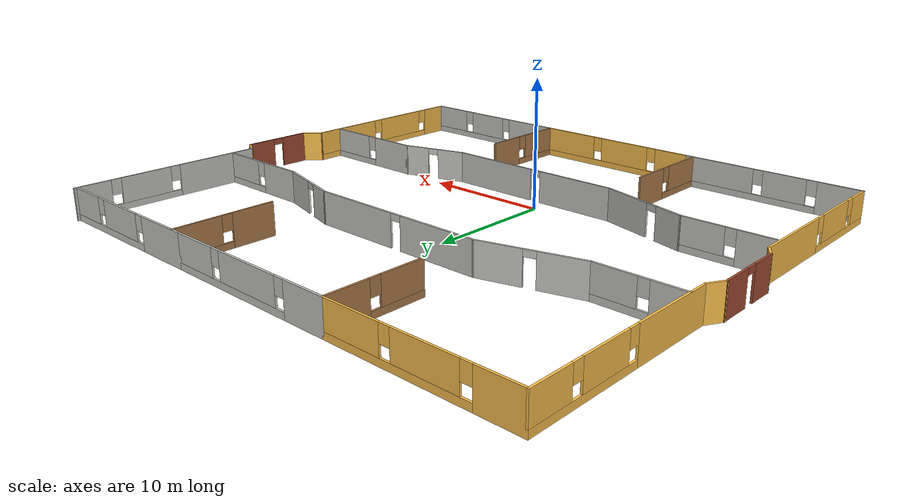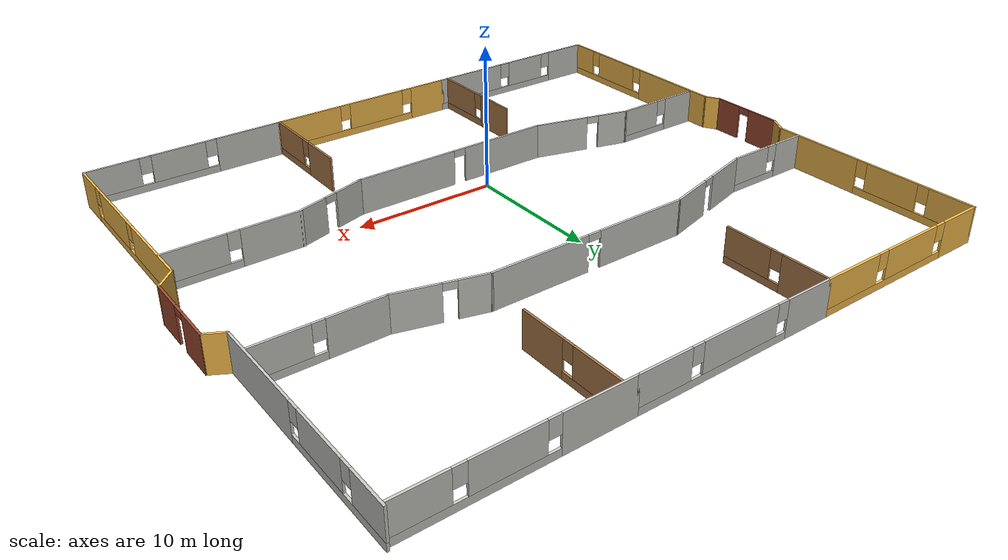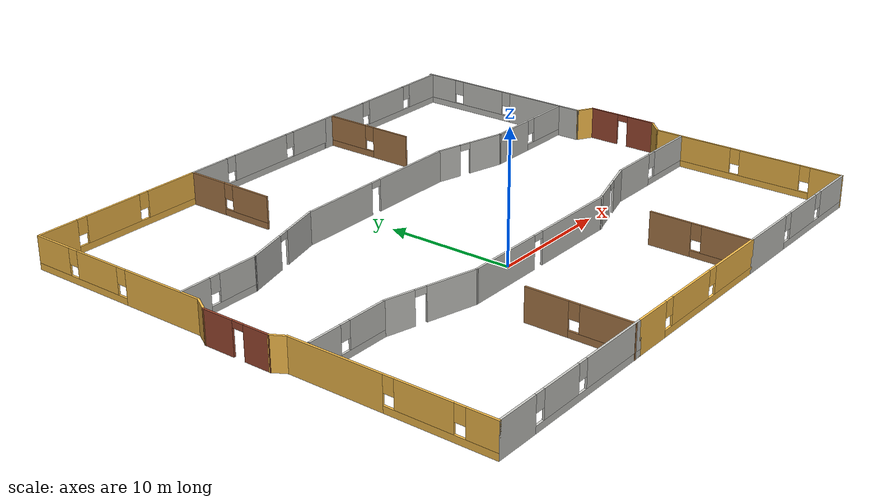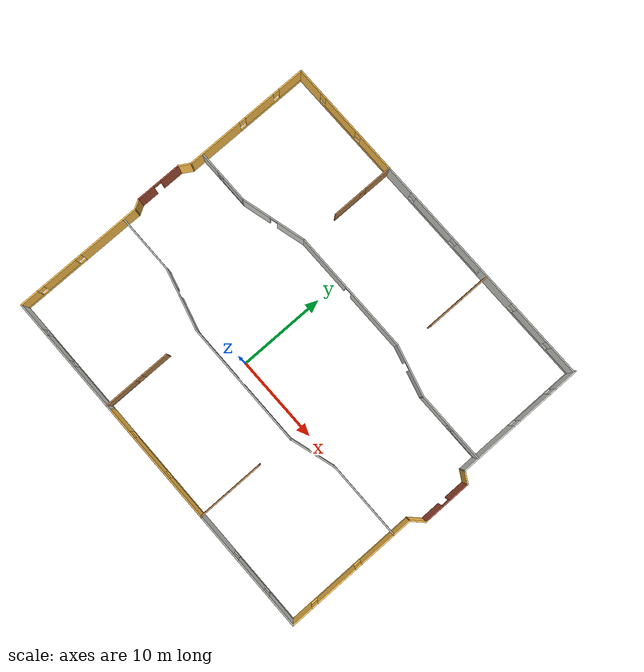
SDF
<?xml version='1.0'?>
<sdf version='1.6'>
  <model name='model'>
    <pose frame=''>2.02965 5.6267 0 0 -0 0</pose>
    <link name='Wall_22'>
      <pose frame=''>-21.3175 -11.3683 0 0 0 -1.5708</pose>
      <visual name='Wall_22_Visual_0'>
        <pose frame=''>-3.98783 0 1.25 0 -0 0</pose>
        <geometry>
          <box>
            <size>7.27435 0.15 2.5</size>
          </box>
        </geometry>
        <material>
          <script>
            <uri>file://media/materials/scripts/gazebo.material</uri>
            <name>Gazebo/Grey</name>
          </script>
          <ambient>1 0.764706 0.305882 1</ambient>
        </material>
        <meta>
          <layer>0</layer>
        </meta>
      </visual>
      <collision name='Wall_22_Collision_0'>
        <geometry>
          <box>
            <size>7.27435 0.15 2.5</size>
          </box>
        </geometry>
        <pose frame=''>-3.98783 0 1.25 0 -0 0</pose>
      </collision>
      <visual name='Wall_22_Visual_1'>
        <pose frame=''>3.63717 0 0.25 0 -0 0</pose>
        <geometry>
          <box>
            <size>7.97565 0.15 0.5</size>
          </box>
        </geometry>
        <material>
          <script>
            <uri>file://media/materials/scripts/gazebo.material</uri>
            <name>Gazebo/Grey</name>
          </script>
          <ambient>1 0.764706 0.305882 1</ambient>
        </material>
        <meta>
          <layer>0</layer>
        </meta>
      </visual>
      <collision name='Wall_22_Collision_1'>
        <geometry>
          <box>
            <size>7.97565 0.15 0.5</size>
          </box>
        </geometry>
        <pose frame=''>3.63717 0 0.25 0 -0 0</pose>
      </collision>
      <visual name='Wall_22_Visual_2'>
        <pose frame=''>2.53115 0 1.5 0 -0 0</pose>
        <geometry>
          <box>
            <size>4.16361 0.15 2</size>
          </box>
        </geometry>
        <material>
          <script>
            <uri>file://media/materials/scripts/gazebo.material</uri>
            <name>Gazebo/Grey</name>
          </script>
          <ambient>1 0.764706 0.305882 1</ambient>
        </material>
        <meta>
          <layer>0</layer>
        </meta>
      </visual>
      <collision name='Wall_22_Collision_2'>
        <geometry>
          <box>
            <size>4.16361 0.15 2</size>
          </box>
        </geometry>
        <pose frame=''>2.53115 0 1.5 0 -0 0</pose>
      </collision>
      <visual name='Wall_22_Visual_3'>
        <pose frame=''>6.51898 0 1.5 0 -0 0</pose>
        <geometry>
          <box>
            <size>2.21204 0.15 2</size>
          </box>
        </geometry>
        <material>
          <script>
            <uri>file://media/materials/scripts/gazebo.material</uri>
            <name>Gazebo/Grey</name>
          </script>
          <ambient>1 0.764706 0.305882 1</ambient>
        </material>
        <meta>
          <layer>0</layer>
        </meta>
      </visual>
      <collision name='Wall_22_Collision_3'>
        <geometry>
          <box>
            <size>2.21204 0.15 2</size>
          </box>
        </geometry>
        <pose frame=''>6.51898 0 1.5 0 -0 0</pose>
      </collision>
      <visual name='Wall_22_Visual_4'>
        <pose frame=''>0.049349 0 1.9 0 -0 0</pose>
        <geometry>
          <box>
            <size>0.8 0.15 1.2</size>
          </box>
        </geometry>
        <material>
          <script>
            <uri>file://media/materials/scripts/gazebo.material</uri>
            <name>Gazebo/Grey</name>
          </script>
          <ambient>1 0.764706 0.305882 1</ambient>
        </material>
        <meta>
          <layer>0</layer>
        </meta>
      </visual>
      <collision name='Wall_22_Collision_4'>
        <geometry>
          <box>
            <size>0.8 0.15 1.2</size>
          </box>
        </geometry>
        <pose frame=''>0.049349 0 1.9 0 -0 0</pose>
      </collision>
      <visual name='Wall_22_Visual_5'>
        <pose frame=''>5.01296 0 1.9 0 -0 0</pose>
        <geometry>
          <box>
            <size>0.8 0.15 1.2</size>
          </box>
        </geometry>
        <material>
          <script>
            <uri>file://media/materials/scripts/gazebo.material</uri>
            <name>Gazebo/Grey</name>
          </script>
          <ambient>1 0.764706 0.305882 1</ambient>
        </material>
        <meta>
          <layer>0</layer>
        </meta>
      </visual>
      <collision name='Wall_22_Collision_5'>
        <geometry>
          <box>
            <size>0.8 0.15 1.2</size>
          </box>
        </geometry>
        <pose frame=''>5.01296 0 1.9 0 -0 0</pose>
      </collision>
    </link>
    <link name='Wall_23'>
      <pose frame=''>-14.2675 -18.9183 0 0 -0 0</pose>
      <visual name='Wall_23_Visual_0'>
        <pose frame=''>-5.44036 0 1.25 0 -0 0</pose>
        <geometry>
          <box>
            <size>3.36928 0.15 2.5</size>
          </box>
        </geometry>
        <material>
          <script>
            <uri>file://media/materials/scripts/gazebo.material</uri>
            <name>Gazebo/CeilingTiled</name>
          </script>
          <ambient>1 0.764706 0.305882 1</ambient>
        </material>
        <meta>
          <layer>0</layer>
        </meta>
      </visual>
      <collision name='Wall_23_Collision_0'>
        <geometry>
          <box>
            <size>3.36928 0.15 2.5</size>
          </box>
        </geometry>
        <pose frame=''>-5.44036 0 1.25 0 -0 0</pose>
      </collision>
      <visual name='Wall_23_Visual_1'>
        <pose frame=''>1.68464 0 0.25 0 -0 0</pose>
        <geometry>
          <box>
            <size>10.8807 0.15 0.5</size>
          </box>
        </geometry>
        <material>
          <script>
            <uri>file://media/materials/scripts/gazebo.material</uri>
            <name>Gazebo/CeilingTiled</name>
          </script>
          <ambient>1 0.764706 0.305882 1</ambient>
        </material>
        <meta>
          <layer>0</layer>
        </meta>
      </visual>
      <collision name='Wall_23_Collision_1'>
        <geometry>
          <box>
            <size>10.8807 0.15 0.5</size>
          </box>
        </geometry>
        <pose frame=''>1.68464 0 0.25 0 -0 0</pose>
      </collision>
      <visual name='Wall_23_Visual_2'>
        <pose frame=''>-1.24407 0 1.5 0 -0 0</pose>
        <geometry>
          <box>
            <size>3.42331 0.15 2</size>
          </box>
        </geometry>
        <material>
          <script>
            <uri>file://media/materials/scripts/gazebo.material</uri>
            <name>Gazebo/CeilingTiled</name>
          </script>
          <ambient>1 0.764706 0.305882 1</ambient>
        </material>
        <meta>
          <layer>0</layer>
        </meta>
      </visual>
      <collision name='Wall_23_Collision_2'>
        <geometry>
          <box>
            <size>3.42331 0.15 2</size>
          </box>
        </geometry>
        <pose frame=''>-1.24407 0 1.5 0 -0 0</pose>
      </collision>
      <visual name='Wall_23_Visual_3'>
        <pose frame=''>4.19629 0 1.5 0 -0 0</pose>
        <geometry>
          <box>
            <size>5.85741 0.15 2</size>
          </box>
        </geometry>
        <material>
          <script>
            <uri>file://media/materials/scripts/gazebo.material</uri>
            <name>Gazebo/CeilingTiled</name>
          </script>
          <ambient>1 0.764706 0.305882 1</ambient>
        </material>
        <meta>
          <layer>0</layer>
        </meta>
      </visual>
      <collision name='Wall_23_Collision_3'>
        <geometry>
          <box>
            <size>5.85741 0.15 2</size>
          </box>
        </geometry>
        <pose frame=''>4.19629 0 1.5 0 -0 0</pose>
      </collision>
      <visual name='Wall_23_Visual_4'>
        <pose frame=''>-3.35572 0 1.9 0 -0 0</pose>
        <geometry>
          <box>
            <size>0.8 0.15 1.2</size>
          </box>
        </geometry>
        <material>
          <script>
            <uri>file://media/materials/scripts/gazebo.material</uri>
            <name>Gazebo/CeilingTiled</name>
          </script>
          <ambient>1 0.764706 0.305882 1</ambient>
        </material>
        <meta>
          <layer>0</layer>
        </meta>
      </visual>
      <collision name='Wall_23_Collision_4'>
        <geometry>
          <box>
            <size>0.8 0.15 1.2</size>
          </box>
        </geometry>
        <pose frame=''>-3.35572 0 1.9 0 -0 0</pose>
      </collision>
      <visual name='Wall_23_Visual_5'>
        <pose frame=''>0.867585 0 1.9 0 -0 0</pose>
        <geometry>
          <box>
            <size>0.8 0.15 1.2</size>
          </box>
        </geometry>
        <material>
          <script>
            <uri>file://media/materials/scripts/gazebo.material</uri>
            <name>Gazebo/CeilingTiled</name>
          </script>
          <ambient>1 0.764706 0.305882 1</ambient>
        </material>
        <meta>
          <layer>0</layer>
        </meta>
      </visual>
      <collision name='Wall_23_Collision_5'>
        <geometry>
          <box>
            <size>0.8 0.15 1.2</size>
          </box>
        </geometry>
        <pose frame=''>0.867585 0 1.9 0 -0 0</pose>
      </collision>
    </link>
    <link name='Wall_24'>
      <pose frame=''>-0.167493 -18.9183 0 0 -0 0</pose>
      <visual name='Wall_24_Visual_0'>
        <pose frame=''>-5.61853 0 1.25 0 -0 0</pose>
        <geometry>
          <box>
            <size>3.01295 0.15 2.5</size>
          </box>
        </geometry>
        <material>
          <script>
            <uri>file://media/materials/scripts/gazebo.material</uri>
            <name>Gazebo/Grey</name>
          </script>
          <ambient>1 0.764706 0.305882 1</ambient>
        </material>
        <meta>
          <layer>0</layer>
        </meta>
      </visual>
      <collision name='Wall_24_Collision_0'>
        <geometry>
          <box>
            <size>3.01295 0.15 2.5</size>
          </box>
        </geometry>
        <pose frame=''>-5.61853 0 1.25 0 -0 0</pose>
      </collision>
      <visual name='Wall_24_Visual_1'>
        <pose frame=''>1.50647 0 0.25 0 -0 0</pose>
        <geometry>
          <box>
            <size>11.2371 0.15 0.5</size>
          </box>
        </geometry>
        <material>
          <script>
            <uri>file://media/materials/scripts/gazebo.material</uri>
            <name>Gazebo/Grey</name>
          </script>
          <ambient>1 0.764706 0.305882 1</ambient>
        </material>
        <meta>
          <layer>0</layer>
        </meta>
      </visual>
      <collision name='Wall_24_Collision_1'>
        <geometry>
          <box>
            <size>11.2371 0.15 0.5</size>
          </box>
        </geometry>
        <pose frame=''>1.50647 0 0.25 0 -0 0</pose>
      </collision>
      <visual name='Wall_24_Visual_2'>
        <pose frame=''>-1.02682 0 1.5 0 -0 0</pose>
        <geometry>
          <box>
            <size>4.57046 0.15 2</size>
          </box>
        </geometry>
        <material>
          <script>
            <uri>file://media/materials/scripts/gazebo.material</uri>
            <name>Gazebo/Grey</name>
          </script>
          <ambient>1 0.764706 0.305882 1</ambient>
        </material>
        <meta>
          <layer>0</layer>
        </meta>
      </visual>
      <collision name='Wall_24_Collision_2'>
        <geometry>
          <box>
            <size>4.57046 0.15 2</size>
          </box>
        </geometry>
        <pose frame=''>-1.02682 0 1.5 0 -0 0</pose>
      </collision>
      <visual name='Wall_24_Visual_3'>
        <pose frame=''>4.5917 0 1.5 0 -0 0</pose>
        <geometry>
          <box>
            <size>5.06659 0.15 2</size>
          </box>
        </geometry>
        <material>
          <script>
            <uri>file://media/materials/scripts/gazebo.material</uri>
            <name>Gazebo/Grey</name>
          </script>
          <ambient>1 0.764706 0.305882 1</ambient>
        </material>
        <meta>
          <layer>0</layer>
        </meta>
      </visual>
      <collision name='Wall_24_Collision_3'>
        <geometry>
          <box>
            <size>5.06659 0.15 2</size>
          </box>
        </geometry>
        <pose frame=''>4.5917 0 1.5 0 -0 0</pose>
      </collision>
      <visual name='Wall_24_Visual_4'>
        <pose frame=''>-3.71205 0 1.9 0 -0 0</pose>
        <geometry>
          <box>
            <size>0.8 0.15 1.2</size>
          </box>
        </geometry>
        <material>
          <script>
            <uri>file://media/materials/scripts/gazebo.material</uri>
            <name>Gazebo/Grey</name>
          </script>
          <ambient>1 0.764706 0.305882 1</ambient>
        </material>
        <meta>
          <layer>0</layer>
        </meta>
      </visual>
      <collision name='Wall_24_Collision_4'>
        <geometry>
          <box>
            <size>0.8 0.15 1.2</size>
          </box>
        </geometry>
        <pose frame=''>-3.71205 0 1.9 0 -0 0</pose>
      </collision>
      <visual name='Wall_24_Visual_5'>
        <pose frame=''>1.65841 0 1.9 0 -0 0</pose>
        <geometry>
          <box>
            <size>0.8 0.15 1.2</size>
          </box>
        </geometry>
        <material>
          <script>
            <uri>file://media/materials/scripts/gazebo.material</uri>
            <name>Gazebo/Grey</name>
          </script>
          <ambient>1 0.764706 0.305882 1</ambient>
        </material>
        <meta>
          <layer>0</layer>
        </meta>
      </visual>
      <collision name='Wall_24_Collision_5'>
        <geometry>
          <box>
            <size>0.8 0.15 1.2</size>
          </box>
        </geometry>
        <pose frame=''>1.65841 0 1.9 0 -0 0</pose>
      </collision>
    </link>
    <link name='Wall_25'>
      <pose frame=''>13.8075 -18.9183 0 0 -0 0</pose>
      <visual name='Wall_25_Visual_0'>
        <pose frame=''>-4.56921 0 1.25 0 -0 0</pose>
        <geometry>
          <box>
            <size>4.86159 0.15 2.5</size>
          </box>
        </geometry>
        <material>
          <script>
            <uri>file://media/materials/scripts/gazebo.material</uri>
            <name>Gazebo/CeilingTiled</name>
          </script>
          <ambient>1 0.764706 0.305882 1</ambient>
        </material>
        <meta>
          <layer>0</layer>
        </meta>
      </visual>
      <collision name='Wall_25_Collision_0'>
        <geometry>
          <box>
            <size>4.86159 0.15 2.5</size>
          </box>
        </geometry>
        <pose frame=''>-4.56921 0 1.25 0 -0 0</pose>
      </collision>
      <visual name='Wall_25_Visual_1'>
        <pose frame=''>2.43079 0 0.25 0 -0 0</pose>
        <geometry>
          <box>
            <size>9.13841 0.15 0.5</size>
          </box>
        </geometry>
        <material>
          <script>
            <uri>file://media/materials/scripts/gazebo.material</uri>
            <name>Gazebo/CeilingTiled</name>
          </script>
          <ambient>1 0.764706 0.305882 1</ambient>
        </material>
        <meta>
          <layer>0</layer>
        </meta>
      </visual>
      <collision name='Wall_25_Collision_1'>
        <geometry>
          <box>
            <size>9.13841 0.15 0.5</size>
          </box>
        </geometry>
        <pose frame=''>2.43079 0 0.25 0 -0 0</pose>
      </collision>
      <visual name='Wall_25_Visual_2'>
        <pose frame=''>0.58065 0 1.5 0 -0 0</pose>
        <geometry>
          <box>
            <size>3.83812 0.15 2</size>
          </box>
        </geometry>
        <material>
          <script>
            <uri>file://media/materials/scripts/gazebo.material</uri>
            <name>Gazebo/CeilingTiled</name>
          </script>
          <ambient>1 0.764706 0.305882 1</ambient>
        </material>
        <meta>
          <layer>0</layer>
        </meta>
      </visual>
      <collision name='Wall_25_Collision_2'>
        <geometry>
          <box>
            <size>3.83812 0.15 2</size>
          </box>
        </geometry>
        <pose frame=''>0.58065 0 1.5 0 -0 0</pose>
      </collision>
      <visual name='Wall_25_Visual_3'>
        <pose frame=''>5.14986 0 1.5 0 -0 0</pose>
        <geometry>
          <box>
            <size>3.70029 0.15 2</size>
          </box>
        </geometry>
        <material>
          <script>
            <uri>file://media/materials/scripts/gazebo.material</uri>
            <name>Gazebo/CeilingTiled</name>
          </script>
          <ambient>1 0.764706 0.305882 1</ambient>
        </material>
        <meta>
          <layer>0</layer>
        </meta>
      </visual>
      <collision name='Wall_25_Collision_3'>
        <geometry>
          <box>
            <size>3.70029 0.15 2</size>
          </box>
        </geometry>
        <pose frame=''>5.14986 0 1.5 0 -0 0</pose>
      </collision>
      <visual name='Wall_25_Visual_4'>
        <pose frame=''>-1.73841 0 1.9 0 -0 0</pose>
        <geometry>
          <box>
            <size>0.8 0.15 1.2</size>
          </box>
        </geometry>
        <material>
          <script>
            <uri>file://media/materials/scripts/gazebo.material</uri>
            <name>Gazebo/CeilingTiled</name>
          </script>
          <ambient>1 0.764706 0.305882 1</ambient>
        </material>
        <meta>
          <layer>0</layer>
        </meta>
      </visual>
      <collision name='Wall_25_Collision_4'>
        <geometry>
          <box>
            <size>0.8 0.15 1.2</size>
          </box>
        </geometry>
        <pose frame=''>-1.73841 0 1.9 0 -0 0</pose>
      </collision>
      <visual name='Wall_25_Visual_5'>
        <pose frame=''>2.89971 0 1.9 0 -0 0</pose>
        <geometry>
          <box>
            <size>0.8 0.15 1.2</size>
          </box>
        </geometry>
        <material>
          <script>
            <uri>file://media/materials/scripts/gazebo.material</uri>
            <name>Gazebo/CeilingTiled</name>
          </script>
          <ambient>1 0.764706 0.305882 1</ambient>
        </material>
        <meta>
          <layer>0</layer>
        </meta>
      </visual>
      <collision name='Wall_25_Collision_5'>
        <geometry>
          <box>
            <size>0.8 0.15 1.2</size>
          </box>
        </geometry>
        <pose frame=''>2.89971 0 1.9 0 -0 0</pose>
      </collision>
    </link>
    <link name='Wall_26'>
      <pose frame=''>20.7325 -11.2433 0 0 -0 1.5708</pose>
      <visual name='Wall_26_Visual_0'>
        <pose frame=''>-6.48124 0 1.25 0 -0 0</pose>
        <geometry>
          <box>
            <size>2.53753 0.15 2.5</size>
          </box>
        </geometry>
        <material>
          <script>
            <uri>file://media/materials/scripts/gazebo.material</uri>
            <name>Gazebo/Grey</name>
          </script>
          <ambient>1 0.764706 0.305882 1</ambient>
        </material>
        <meta>
          <layer>0</layer>
        </meta>
      </visual>
      <collision name='Wall_26_Collision_0'>
        <geometry>
          <box>
            <size>2.53753 0.15 2.5</size>
          </box>
        </geometry>
        <pose frame=''>-6.48124 0 1.25 0 -0 0</pose>
      </collision>
      <visual name='Wall_26_Visual_1'>
        <pose frame=''>1.26876 0 0.25 0 -0 0</pose>
        <geometry>
          <box>
            <size>12.9625 0.15 0.5</size>
          </box>
        </geometry>
        <material>
          <script>
            <uri>file://media/materials/scripts/gazebo.material</uri>
            <name>Gazebo/Grey</name>
          </script>
          <ambient>1 0.764706 0.305882 1</ambient>
        </material>
        <meta>
          <layer>0</layer>
        </meta>
      </visual>
      <collision name='Wall_26_Collision_1'>
        <geometry>
          <box>
            <size>12.9625 0.15 0.5</size>
          </box>
        </geometry>
        <pose frame=''>1.26876 0 0.25 0 -0 0</pose>
      </collision>
      <visual name='Wall_26_Visual_2'>
        <pose frame=''>-1.95201 0 1.5 0 -0 0</pose>
        <geometry>
          <box>
            <size>4.92092 0.15 2</size>
          </box>
        </geometry>
        <material>
          <script>
            <uri>file://media/materials/scripts/gazebo.material</uri>
            <name>Gazebo/Grey</name>
          </script>
          <ambient>1 0.764706 0.305882 1</ambient>
        </material>
        <meta>
          <layer>0</layer>
        </meta>
      </visual>
      <collision name='Wall_26_Collision_2'>
        <geometry>
          <box>
            <size>4.92092 0.15 2</size>
          </box>
        </geometry>
        <pose frame=''>-1.95201 0 1.5 0 -0 0</pose>
      </collision>
      <visual name='Wall_26_Visual_3'>
        <pose frame=''>4.52922 0 1.5 0 -0 0</pose>
        <geometry>
          <box>
            <size>6.44155 0.15 2</size>
          </box>
        </geometry>
        <material>
          <script>
            <uri>file://media/materials/scripts/gazebo.material</uri>
            <name>Gazebo/Grey</name>
          </script>
          <ambient>1 0.764706 0.305882 1</ambient>
        </material>
        <meta>
          <layer>0</layer>
        </meta>
      </visual>
      <collision name='Wall_26_Collision_3'>
        <geometry>
          <box>
            <size>6.44155 0.15 2</size>
          </box>
        </geometry>
        <pose frame=''>4.52922 0 1.5 0 -0 0</pose>
      </collision>
      <visual name='Wall_26_Visual_4'>
        <pose frame=''>-4.81247 0 1.9 0 -0 0</pose>
        <geometry>
          <box>
            <size>0.8 0.15 1.2</size>
          </box>
        </geometry>
        <material>
          <script>
            <uri>file://media/materials/scripts/gazebo.material</uri>
            <name>Gazebo/Grey</name>
          </script>
          <ambient>1 0.764706 0.305882 1</ambient>
        </material>
        <meta>
          <layer>0</layer>
        </meta>
      </visual>
      <collision name='Wall_26_Collision_4'>
        <geometry>
          <box>
            <size>0.8 0.15 1.2</size>
          </box>
        </geometry>
        <pose frame=''>-4.81247 0 1.9 0 -0 0</pose>
      </collision>
      <visual name='Wall_26_Visual_5'>
        <pose frame=''>0.908446 0 1.9 0 -0 0</pose>
        <geometry>
          <box>
            <size>0.8 0.15 1.2</size>
          </box>
        </geometry>
        <material>
          <script>
            <uri>file://media/materials/scripts/gazebo.material</uri>
            <name>Gazebo/Grey</name>
          </script>
          <ambient>1 0.764706 0.305882 1</ambient>
        </material>
        <meta>
          <layer>0</layer>
        </meta>
      </visual>
      <collision name='Wall_26_Collision_5'>
        <geometry>
          <box>
            <size>0.8 0.15 1.2</size>
          </box>
        </geometry>
        <pose frame=''>0.908446 0 1.9 0 -0 0</pose>
      </collision>
    </link>
    <link name='Wall_27'>
      <collision name='Wall_27_Collision'>
        <geometry>
          <box>
            <size>1.75 0.15 2.5</size>
          </box>
        </geometry>
        <pose frame=''>0 0 1.25 0 -0 0</pose>
      </collision>
      <visual name='Wall_27_Visual'>
        <pose frame=''>0 0 1.25 0 -0 0</pose>
        <geometry>
          <box>
            <size>1.75 0.15 2.5</size>
          </box>
        </geometry>
        <material>
          <script>
            <uri>file://media/materials/scripts/gazebo.material</uri>
            <name>Gazebo/Grey</name>
          </script>
          <ambient>1 0.764706 0.305882 1</ambient>
        </material>
        <meta>
          <layer>0</layer>
        </meta>
      </visual>
      <pose frame=''>21.2982 -3.00259 0 0 -0 0.785398</pose>
    </link>
    <link name='Wall_28'>
      <pose frame=''>21.8639 0.363092 0 0 -0 1.5708</pose>
      <visual name='Wall_28_Visual_0'>
        <pose frame=''>-1.69424 0 1.25 0 -0 0</pose>
        <geometry>
          <box>
            <size>2.36151 0.15 2.5</size>
          </box>
        </geometry>
        <material>
          <script>
            <uri>file://media/materials/scripts/gazebo.material</uri>
            <name>Gazebo/Bricks</name>
          </script>
          <ambient>1 1 1 1</ambient>
        </material>
        <meta>
          <layer>0</layer>
        </meta>
      </visual>
      <collision name='Wall_28_Collision_0'>
        <geometry>
          <box>
            <size>2.36151 0.15 2.5</size>
          </box>
        </geometry>
        <pose frame=''>-1.69424 0 1.25 0 -0 0</pose>
      </collision>
      <visual name='Wall_28_Visual_1'>
        <pose frame=''>1.63076 0 1.25 0 -0 0</pose>
        <geometry>
          <box>
            <size>2.48849 0.15 2.5</size>
          </box>
        </geometry>
        <material>
          <script>
            <uri>file://media/materials/scripts/gazebo.material</uri>
            <name>Gazebo/Bricks</name>
          </script>
          <ambient>1 1 1 1</ambient>
        </material>
        <meta>
          <layer>0</layer>
        </meta>
      </visual>
      <collision name='Wall_28_Collision_1'>
        <geometry>
          <box>
            <size>2.48849 0.15 2.5</size>
          </box>
        </geometry>
        <pose frame=''>1.63076 0 1.25 0 -0 0</pose>
      </collision>
      <visual name='Wall_28_Visual_2'>
        <pose frame=''>-0.063486 0 2.25 0 -0 0</pose>
        <geometry>
          <box>
            <size>0.9 0.15 0.5</size>
          </box>
        </geometry>
        <material>
          <script>
            <uri>file://media/materials/scripts/gazebo.material</uri>
            <name>Gazebo/Bricks</name>
          </script>
          <ambient>1 1 1 1</ambient>
        </material>
        <meta>
          <layer>0</layer>
        </meta>
      </visual>
      <collision name='Wall_28_Collision_2'>
        <geometry>
          <box>
            <size>0.9 0.15 0.5</size>
          </box>
        </geometry>
        <pose frame=''>-0.063486 0 2.25 0 -0 0</pose>
      </collision>
    </link>
    <link name='Wall_29'>
      <collision name='Wall_29_Collision'>
        <geometry>
          <box>
            <size>1.5 0.15 2.5</size>
          </box>
        </geometry>
        <pose frame=''>0 0 1.25 0 -0 0</pose>
      </collision>
      <visual name='Wall_29_Visual'>
        <pose frame=''>0 0 1.25 0 -0 0</pose>
        <geometry>
          <box>
            <size>1.5 0.15 2.5</size>
          </box>
        </geometry>
        <material>
          <script>
            <uri>file://media/materials/scripts/gazebo.material</uri>
            <name>Gazebo/Grey</name>
          </script>
          <ambient>1 0.764706 0.305882 1</ambient>
        </material>
        <meta>
          <layer>0</layer>
        </meta>
      </visual>
      <pose frame=''>21.2793 3.50059 0 0 -0 2.61799</pose>
    </link>
    <link name='Wall_36'>
      <collision name='Wall_36_Collision'>
        <geometry>
          <box>
            <size>1.25 0.15 2.5</size>
          </box>
        </geometry>
        <pose frame=''>0 0 1.25 0 -0 0</pose>
      </collision>
      <visual name='Wall_36_Visual'>
        <pose frame=''>0 0 1.25 0 -0 0</pose>
        <geometry>
          <box>
            <size>1.25 0.15 2.5</size>
          </box>
        </geometry>
        <material>
          <script>
            <uri>file://media/materials/scripts/gazebo.material</uri>
            <name>Gazebo/Grey</name>
          </script>
          <ambient>1 0.764706 0.305882 1</ambient>
        </material>
        <meta>
          <layer>0</layer>
        </meta>
      </visual>
      <pose frame=''>-21.5925 -3.34197 0 0 -0 2.0944</pose>
    </link>
    <link name='Wall_37'>
      <pose frame=''>-21.8675 -0.190651 0 0 -0 1.5708</pose>
      <visual name='Wall_37_Visual_0'>
        <pose frame=''>-1.69498 0 1.25 0 -0 0</pose>
        <geometry>
          <box>
            <size>2.11003 0.15 2.5</size>
          </box>
        </geometry>
        <material>
          <script>
            <uri>file://media/materials/scripts/gazebo.material</uri>
            <name>Gazebo/Bricks</name>
          </script>
          <ambient>1 1 1 1</ambient>
        </material>
        <meta>
          <layer>0</layer>
        </meta>
      </visual>
      <collision name='Wall_37_Collision_0'>
        <geometry>
          <box>
            <size>2.11003 0.15 2.5</size>
          </box>
        </geometry>
        <pose frame=''>-1.69498 0 1.25 0 -0 0</pose>
      </collision>
      <visual name='Wall_37_Visual_1'>
        <pose frame=''>1.50502 0 1.25 0 -0 0</pose>
        <geometry>
          <box>
            <size>2.48997 0.15 2.5</size>
          </box>
        </geometry>
        <material>
          <script>
            <uri>file://media/materials/scripts/gazebo.material</uri>
            <name>Gazebo/Bricks</name>
          </script>
          <ambient>1 1 1 1</ambient>
        </material>
        <meta>
          <layer>0</layer>
        </meta>
      </visual>
      <collision name='Wall_37_Collision_1'>
        <geometry>
          <box>
            <size>2.48997 0.15 2.5</size>
          </box>
        </geometry>
        <pose frame=''>1.50502 0 1.25 0 -0 0</pose>
      </collision>
      <visual name='Wall_37_Visual_2'>
        <pose frame=''>-0.189968 0 2.25 0 -0 0</pose>
        <geometry>
          <box>
            <size>0.9 0.15 0.5</size>
          </box>
        </geometry>
        <material>
          <script>
            <uri>file://media/materials/scripts/gazebo.material</uri>
            <name>Gazebo/Bricks</name>
          </script>
          <ambient>1 1 1 1</ambient>
        </material>
        <meta>
          <layer>0</layer>
        </meta>
      </visual>
      <collision name='Wall_37_Collision_2'>
        <geometry>
          <box>
            <size>0.9 0.15 0.5</size>
          </box>
        </geometry>
        <pose frame=''>-0.189968 0 2.25 0 -0 0</pose>
      </collision>
    </link>
    <link name='Wall_38'>
      <collision name='Wall_38_Collision'>
        <geometry>
          <box>
            <size>1.5 0.15 2.5</size>
          </box>
        </geometry>
        <pose frame=''>0 0 1.25 0 -0 0</pose>
      </collision>
      <visual name='Wall_38_Visual'>
        <pose frame=''>0 0 1.25 0 -0 0</pose>
        <geometry>
          <box>
            <size>1.5 0.15 2.5</size>
          </box>
        </geometry>
        <material>
          <script>
            <uri>file://media/materials/scripts/gazebo.material</uri>
            <name>Gazebo/Grey</name>
          </script>
          <ambient>1 0.764706 0.305882 1</ambient>
        </material>
        <meta>
          <layer>0</layer>
        </meta>
      </visual>
      <pose frame=''>-21.53 3.06892 0 0 -0 1.0472</pose>
    </link>
    <link name='Wall_40'>
      <pose frame=''>-21.1925 11.2035 0 0 -0 1.5708</pose>
      <visual name='Wall_40_Visual_0'>
        <pose frame=''>-4.29734 0 1.25 0 -0 0</pose>
        <geometry>
          <box>
            <size>6.65533 0.15 2.5</size>
          </box>
        </geometry>
        <material>
          <script>
            <uri>file://media/materials/scripts/gazebo.material</uri>
            <name>Gazebo/Grey</name>
          </script>
          <ambient>1 0.764706 0.305882 1</ambient>
        </material>
        <meta>
          <layer>0</layer>
        </meta>
      </visual>
      <collision name='Wall_40_Collision_0'>
        <geometry>
          <box>
            <size>6.65533 0.15 2.5</size>
          </box>
        </geometry>
        <pose frame=''>-4.29734 0 1.25 0 -0 0</pose>
      </collision>
      <visual name='Wall_40_Visual_1'>
        <pose frame=''>3.32766 0 0.25 0 -0 0</pose>
        <geometry>
          <box>
            <size>8.59467 0.15 0.5</size>
          </box>
        </geometry>
        <material>
          <script>
            <uri>file://media/materials/scripts/gazebo.material</uri>
            <name>Gazebo/Grey</name>
          </script>
          <ambient>1 0.764706 0.305882 1</ambient>
        </material>
        <meta>
          <layer>0</layer>
        </meta>
      </visual>
      <collision name='Wall_40_Collision_1'>
        <geometry>
          <box>
            <size>8.59467 0.15 0.5</size>
          </box>
        </geometry>
        <pose frame=''>3.32766 0 0.25 0 -0 0</pose>
      </collision>
      <visual name='Wall_40_Visual_2'>
        <pose frame=''>1.74939 0 1.5 0 -0 0</pose>
        <geometry>
          <box>
            <size>3.83812 0.15 2</size>
          </box>
        </geometry>
        <material>
          <script>
            <uri>file://media/materials/scripts/gazebo.material</uri>
            <name>Gazebo/Grey</name>
          </script>
          <ambient>1 0.764706 0.305882 1</ambient>
        </material>
        <meta>
          <layer>0</layer>
        </meta>
      </visual>
      <collision name='Wall_40_Collision_2'>
        <geometry>
          <box>
            <size>3.83812 0.15 2</size>
          </box>
        </geometry>
        <pose frame=''>1.74939 0 1.5 0 -0 0</pose>
      </collision>
      <visual name='Wall_40_Visual_3'>
        <pose frame=''>6.04673 0 1.5 0 -0 0</pose>
        <geometry>
          <box>
            <size>3.15655 0.15 2</size>
          </box>
        </geometry>
        <material>
          <script>
            <uri>file://media/materials/scripts/gazebo.material</uri>
            <name>Gazebo/Grey</name>
          </script>
          <ambient>1 0.764706 0.305882 1</ambient>
        </material>
        <meta>
          <layer>0</layer>
        </meta>
      </visual>
      <collision name='Wall_40_Collision_3'>
        <geometry>
          <box>
            <size>3.15655 0.15 2</size>
          </box>
        </geometry>
        <pose frame=''>6.04673 0 1.5 0 -0 0</pose>
      </collision>
      <visual name='Wall_40_Visual_4'>
        <pose frame=''>-0.569674 0 1.9 0 -0 0</pose>
        <geometry>
          <box>
            <size>0.8 0.15 1.2</size>
          </box>
        </geometry>
        <material>
          <script>
            <uri>file://media/materials/scripts/gazebo.material</uri>
            <name>Gazebo/Grey</name>
          </script>
          <ambient>1 0.764706 0.305882 1</ambient>
        </material>
        <meta>
          <layer>0</layer>
        </meta>
      </visual>
      <collision name='Wall_40_Collision_4'>
        <geometry>
          <box>
            <size>0.8 0.15 1.2</size>
          </box>
        </geometry>
        <pose frame=''>-0.569674 0 1.9 0 -0 0</pose>
      </collision>
      <visual name='Wall_40_Visual_5'>
        <pose frame=''>4.06845 0 1.9 0 -0 0</pose>
        <geometry>
          <box>
            <size>0.8 0.15 1.2</size>
          </box>
        </geometry>
        <material>
          <script>
            <uri>file://media/materials/scripts/gazebo.material</uri>
            <name>Gazebo/Grey</name>
          </script>
          <ambient>1 0.764706 0.305882 1</ambient>
        </material>
        <meta>
          <layer>0</layer>
        </meta>
      </visual>
      <collision name='Wall_40_Collision_5'>
        <geometry>
          <box>
            <size>0.8 0.15 1.2</size>
          </box>
        </geometry>
        <pose frame=''>4.06845 0 1.9 0 -0 0</pose>
      </collision>
    </link>
    <link name='Wall_42'>
      <pose frame=''>20.6947 11.3881 0 0 -0 1.5708</pose>
      <visual name='Wall_42_Visual_0'>
        <pose frame=''>-4.22815 0 1.25 0 -0 0</pose>
        <geometry>
          <box>
            <size>6.7937 0.15 2.5</size>
          </box>
        </geometry>
        <material>
          <script>
            <uri>file://media/materials/scripts/gazebo.material</uri>
            <name>Gazebo/CeilingTiled</name>
          </script>
          <ambient>1 0.764706 0.305882 1</ambient>
        </material>
        <meta>
          <layer>0</layer>
        </meta>
      </visual>
      <collision name='Wall_42_Collision_0'>
        <geometry>
          <box>
            <size>6.7937 0.15 2.5</size>
          </box>
        </geometry>
        <pose frame=''>-4.22815 0 1.25 0 -0 0</pose>
      </collision>
      <visual name='Wall_42_Visual_1'>
        <pose frame=''>3.39685 0 0.25 0 -0 0</pose>
        <geometry>
          <box>
            <size>8.4563 0.15 0.5</size>
          </box>
        </geometry>
        <material>
          <script>
            <uri>file://media/materials/scripts/gazebo.material</uri>
            <name>Gazebo/CeilingTiled</name>
          </script>
          <ambient>1 0.764706 0.305882 1</ambient>
        </material>
        <meta>
          <layer>0</layer>
        </meta>
      </visual>
      <collision name='Wall_42_Collision_1'>
        <geometry>
          <box>
            <size>8.4563 0.15 0.5</size>
          </box>
        </geometry>
        <pose frame=''>3.39685 0 0.25 0 -0 0</pose>
      </collision>
      <visual name='Wall_42_Visual_2'>
        <pose frame=''>2.00082 0 1.5 0 -0 0</pose>
        <geometry>
          <box>
            <size>4.06425 0.15 2</size>
          </box>
        </geometry>
        <material>
          <script>
            <uri>file://media/materials/scripts/gazebo.material</uri>
            <name>Gazebo/CeilingTiled</name>
          </script>
          <ambient>1 0.764706 0.305882 1</ambient>
        </material>
        <meta>
          <layer>0</layer>
        </meta>
      </visual>
      <collision name='Wall_42_Collision_2'>
        <geometry>
          <box>
            <size>4.06425 0.15 2</size>
          </box>
        </geometry>
        <pose frame=''>2.00082 0 1.5 0 -0 0</pose>
      </collision>
      <visual name='Wall_42_Visual_3'>
        <pose frame=''>6.22897 0 1.5 0 -0 0</pose>
        <geometry>
          <box>
            <size>2.79205 0.15 2</size>
          </box>
        </geometry>
        <material>
          <script>
            <uri>file://media/materials/scripts/gazebo.material</uri>
            <name>Gazebo/CeilingTiled</name>
          </script>
          <ambient>1 0.764706 0.305882 1</ambient>
        </material>
        <meta>
          <layer>0</layer>
        </meta>
      </visual>
      <collision name='Wall_42_Collision_3'>
        <geometry>
          <box>
            <size>2.79205 0.15 2</size>
          </box>
        </geometry>
        <pose frame=''>6.22897 0 1.5 0 -0 0</pose>
      </collision>
      <visual name='Wall_42_Visual_4'>
        <pose frame=''>-0.431303 0 1.9 0 -0 0</pose>
        <geometry>
          <box>
            <size>0.8 0.15 1.2</size>
          </box>
        </geometry>
        <material>
          <script>
            <uri>file://media/materials/scripts/gazebo.material</uri>
            <name>Gazebo/CeilingTiled</name>
          </script>
          <ambient>1 0.764706 0.305882 1</ambient>
        </material>
        <meta>
          <layer>0</layer>
        </meta>
      </visual>
      <collision name='Wall_42_Collision_4'>
        <geometry>
          <box>
            <size>0.8 0.15 1.2</size>
          </box>
        </geometry>
        <pose frame=''>-0.431303 0 1.9 0 -0 0</pose>
      </collision>
      <visual name='Wall_42_Visual_5'>
        <pose frame=''>4.43295 0 1.9 0 -0 0</pose>
        <geometry>
          <box>
            <size>0.8 0.15 1.2</size>
          </box>
        </geometry>
        <material>
          <script>
            <uri>file://media/materials/scripts/gazebo.material</uri>
            <name>Gazebo/CeilingTiled</name>
          </script>
          <ambient>1 0.764706 0.305882 1</ambient>
        </material>
        <meta>
          <layer>0</layer>
        </meta>
      </visual>
      <collision name='Wall_42_Collision_5'>
        <geometry>
          <box>
            <size>0.8 0.15 1.2</size>
          </box>
        </geometry>
        <pose frame=''>4.43295 0 1.9 0 -0 0</pose>
      </collision>
    </link>
    <link name='Wall_51'>
      <pose frame=''>-14.2675 18.7535 0 0 -0 0</pose>
      <visual name='Wall_51_Visual_0'>
        <pose frame=''>-5.3786 0 1.25 0 -0 0</pose>
        <geometry>
          <box>
            <size>3.2428 0.15 2.5</size>
          </box>
        </geometry>
        <material>
          <script>
            <uri>file://media/materials/scripts/gazebo.material</uri>
            <name>Gazebo/Grey</name>
          </script>
          <ambient>1 0.764706 0.305882 1</ambient>
        </material>
        <meta>
          <layer>0</layer>
        </meta>
      </visual>
      <collision name='Wall_51_Collision_0'>
        <geometry>
          <box>
            <size>3.2428 0.15 2.5</size>
          </box>
        </geometry>
        <pose frame=''>-5.3786 0 1.25 0 -0 0</pose>
      </collision>
      <visual name='Wall_51_Visual_1'>
        <pose frame=''>1.6214 0 0.25 0 -0 0</pose>
        <geometry>
          <box>
            <size>10.7572 0.15 0.5</size>
          </box>
        </geometry>
        <material>
          <script>
            <uri>file://media/materials/scripts/gazebo.material</uri>
            <name>Gazebo/Grey</name>
          </script>
          <ambient>1 0.764706 0.305882 1</ambient>
        </material>
        <meta>
          <layer>0</layer>
        </meta>
      </visual>
      <collision name='Wall_51_Collision_1'>
        <geometry>
          <box>
            <size>10.7572 0.15 0.5</size>
          </box>
        </geometry>
        <pose frame=''>1.6214 0 0.25 0 -0 0</pose>
      </collision>
      <visual name='Wall_51_Visual_2'>
        <pose frame=''>-0.618681 0 1.5 0 -0 0</pose>
        <geometry>
          <box>
            <size>4.67704 0.15 2</size>
          </box>
        </geometry>
        <material>
          <script>
            <uri>file://media/materials/scripts/gazebo.material</uri>
            <name>Gazebo/Grey</name>
          </script>
          <ambient>1 0.764706 0.305882 1</ambient>
        </material>
        <meta>
          <layer>0</layer>
        </meta>
      </visual>
      <collision name='Wall_51_Collision_2'>
        <geometry>
          <box>
            <size>4.67704 0.15 2</size>
          </box>
        </geometry>
        <pose frame=''>-0.618681 0 1.5 0 -0 0</pose>
      </collision>
      <visual name='Wall_51_Visual_3'>
        <pose frame=''>4.75992 0 1.5 0 -0 0</pose>
        <geometry>
          <box>
            <size>4.48016 0.15 2</size>
          </box>
        </geometry>
        <material>
          <script>
            <uri>file://media/materials/scripts/gazebo.material</uri>
            <name>Gazebo/Grey</name>
          </script>
          <ambient>1 0.764706 0.305882 1</ambient>
        </material>
        <meta>
          <layer>0</layer>
        </meta>
      </visual>
      <collision name='Wall_51_Collision_3'>
        <geometry>
          <box>
            <size>4.48016 0.15 2</size>
          </box>
        </geometry>
        <pose frame=''>4.75992 0 1.5 0 -0 0</pose>
      </collision>
      <visual name='Wall_51_Visual_4'>
        <pose frame=''>-3.3572 0 1.9 0 -0 0</pose>
        <geometry>
          <box>
            <size>0.8 0.15 1.2</size>
          </box>
        </geometry>
        <material>
          <script>
            <uri>file://media/materials/scripts/gazebo.material</uri>
            <name>Gazebo/Grey</name>
          </script>
          <ambient>1 0.764706 0.305882 1</ambient>
        </material>
        <meta>
          <layer>0</layer>
        </meta>
      </visual>
      <collision name='Wall_51_Collision_4'>
        <geometry>
          <box>
            <size>0.8 0.15 1.2</size>
          </box>
        </geometry>
        <pose frame=''>-3.3572 0 1.9 0 -0 0</pose>
      </collision>
      <visual name='Wall_51_Visual_5'>
        <pose frame=''>2.11984 0 1.9 0 -0 0</pose>
        <geometry>
          <box>
            <size>0.8 0.15 1.2</size>
          </box>
        </geometry>
        <material>
          <script>
            <uri>file://media/materials/scripts/gazebo.material</uri>
            <name>Gazebo/Grey</name>
          </script>
          <ambient>1 0.764706 0.305882 1</ambient>
        </material>
        <meta>
          <layer>0</layer>
        </meta>
      </visual>
      <collision name='Wall_51_Collision_5'>
        <geometry>
          <box>
            <size>0.8 0.15 1.2</size>
          </box>
        </geometry>
        <pose frame=''>2.11984 0 1.9 0 -0 0</pose>
      </collision>
    </link>
    <link name='Wall_52'>
      <pose frame=''>-0.292493 18.7535 0 0 -0 0</pose>
      <visual name='Wall_52_Visual_0'>
        <pose frame=''>-5.39608 0 1.25 0 -0 0</pose>
        <geometry>
          <box>
            <size>3.45785 0.15 2.5</size>
          </box>
        </geometry>
        <material>
          <script>
            <uri>file://media/materials/scripts/gazebo.material</uri>
            <name>Gazebo/CeilingTiled</name>
          </script>
          <ambient>1 0.764706 0.305882 1</ambient>
        </material>
        <meta>
          <layer>0</layer>
        </meta>
      </visual>
      <collision name='Wall_52_Collision_0'>
        <geometry>
          <box>
            <size>3.45785 0.15 2.5</size>
          </box>
        </geometry>
        <pose frame=''>-5.39608 0 1.25 0 -0 0</pose>
      </collision>
      <visual name='Wall_52_Visual_1'>
        <pose frame=''>1.72892 0 0.25 0 -0 0</pose>
        <geometry>
          <box>
            <size>10.7922 0.15 0.5</size>
          </box>
        </geometry>
        <material>
          <script>
            <uri>file://media/materials/scripts/gazebo.material</uri>
            <name>Gazebo/CeilingTiled</name>
          </script>
          <ambient>1 0.764706 0.305882 1</ambient>
        </material>
        <meta>
          <layer>0</layer>
        </meta>
      </visual>
      <collision name='Wall_52_Collision_1'>
        <geometry>
          <box>
            <size>10.7922 0.15 0.5</size>
          </box>
        </geometry>
        <pose frame=''>1.72892 0 0.25 0 -0 0</pose>
      </collision>
      <visual name='Wall_52_Visual_2'>
        <pose frame=''>-0.115746 0 1.5 0 -0 0</pose>
        <geometry>
          <box>
            <size>5.50281 0.15 2</size>
          </box>
        </geometry>
        <material>
          <script>
            <uri>file://media/materials/scripts/gazebo.material</uri>
            <name>Gazebo/CeilingTiled</name>
          </script>
          <ambient>1 0.764706 0.305882 1</ambient>
        </material>
        <meta>
          <layer>0</layer>
        </meta>
      </visual>
      <collision name='Wall_52_Collision_2'>
        <geometry>
          <box>
            <size>5.50281 0.15 2</size>
          </box>
        </geometry>
        <pose frame=''>-0.115746 0 1.5 0 -0 0</pose>
      </collision>
      <visual name='Wall_52_Visual_3'>
        <pose frame=''>5.28033 0 1.5 0 -0 0</pose>
        <geometry>
          <box>
            <size>3.68934 0.15 2</size>
          </box>
        </geometry>
        <material>
          <script>
            <uri>file://media/materials/scripts/gazebo.material</uri>
            <name>Gazebo/CeilingTiled</name>
          </script>
          <ambient>1 0.764706 0.305882 1</ambient>
        </material>
        <meta>
          <layer>0</layer>
        </meta>
      </visual>
      <collision name='Wall_52_Collision_3'>
        <geometry>
          <box>
            <size>3.68934 0.15 2</size>
          </box>
        </geometry>
        <pose frame=''>5.28033 0 1.5 0 -0 0</pose>
      </collision>
      <visual name='Wall_52_Visual_4'>
        <pose frame=''>-3.26715 0 1.9 0 -0 0</pose>
        <geometry>
          <box>
            <size>0.8 0.15 1.2</size>
          </box>
        </geometry>
        <material>
          <script>
            <uri>file://media/materials/scripts/gazebo.material</uri>
            <name>Gazebo/CeilingTiled</name>
          </script>
          <ambient>1 0.764706 0.305882 1</ambient>
        </material>
        <meta>
          <layer>0</layer>
        </meta>
      </visual>
      <collision name='Wall_52_Collision_4'>
        <geometry>
          <box>
            <size>0.8 0.15 1.2</size>
          </box>
        </geometry>
        <pose frame=''>-3.26715 0 1.9 0 -0 0</pose>
      </collision>
      <visual name='Wall_52_Visual_5'>
        <pose frame=''>3.03566 0 1.9 0 -0 0</pose>
        <geometry>
          <box>
            <size>0.8 0.15 1.2</size>
          </box>
        </geometry>
        <material>
          <script>
            <uri>file://media/materials/scripts/gazebo.material</uri>
            <name>Gazebo/CeilingTiled</name>
          </script>
          <ambient>1 0.764706 0.305882 1</ambient>
        </material>
        <meta>
          <layer>0</layer>
        </meta>
      </visual>
      <collision name='Wall_52_Collision_5'>
        <geometry>
          <box>
            <size>0.8 0.15 1.2</size>
          </box>
        </geometry>
        <pose frame=''>3.03566 0 1.9 0 -0 0</pose>
      </collision>
    </link>
    <link name='Wall_53'>
      <pose frame=''>13.6825 18.7535 0 0 -0 0</pose>
      <visual name='Wall_53_Visual_0'>
        <pose frame=''>-4.64128 0 1.25 0 -0 0</pose>
        <geometry>
          <box>
            <size>4.71744 0.15 2.5</size>
          </box>
        </geometry>
        <material>
          <script>
            <uri>file://media/materials/scripts/gazebo.material</uri>
            <name>Gazebo/CeilingTiled</name>
          </script>
          <ambient>1 0.764706 0.305882 1</ambient>
        </material>
        <meta>
          <layer>0</layer>
        </meta>
      </visual>
      <collision name='Wall_53_Collision_0'>
        <geometry>
          <box>
            <size>4.71744 0.15 2.5</size>
          </box>
        </geometry>
        <pose frame=''>-4.64128 0 1.25 0 -0 0</pose>
      </collision>
      <visual name='Wall_53_Visual_1'>
        <pose frame=''>2.35872 0 0.25 0 -0 0</pose>
        <geometry>
          <box>
            <size>9.28256 0.15 0.5</size>
          </box>
        </geometry>
        <material>
          <script>
            <uri>file://media/materials/scripts/gazebo.material</uri>
            <name>Gazebo/CeilingTiled</name>
          </script>
          <ambient>1 0.764706 0.305882 1</ambient>
        </material>
        <meta>
          <layer>0</layer>
        </meta>
      </visual>
      <collision name='Wall_53_Collision_1'>
        <geometry>
          <box>
            <size>9.28256 0.15 0.5</size>
          </box>
        </geometry>
        <pose frame=''>2.35872 0 0.25 0 -0 0</pose>
      </collision>
      <visual name='Wall_53_Visual_2'>
        <pose frame=''>0.700074 0 1.5 0 -0 0</pose>
        <geometry>
          <box>
            <size>4.36526 0.15 2</size>
          </box>
        </geometry>
        <material>
          <script>
            <uri>file://media/materials/scripts/gazebo.material</uri>
            <name>Gazebo/CeilingTiled</name>
          </script>
          <ambient>1 0.764706 0.305882 1</ambient>
        </material>
        <meta>
          <layer>0</layer>
        </meta>
      </visual>
      <collision name='Wall_53_Collision_2'>
        <geometry>
          <box>
            <size>4.36526 0.15 2</size>
          </box>
        </geometry>
        <pose frame=''>0.700074 0 1.5 0 -0 0</pose>
      </collision>
      <visual name='Wall_53_Visual_3'>
        <pose frame=''>5.34135 0 1.5 0 -0 0</pose>
        <geometry>
          <box>
            <size>3.31729 0.15 2</size>
          </box>
        </geometry>
        <material>
          <script>
            <uri>file://media/materials/scripts/gazebo.material</uri>
            <name>Gazebo/CeilingTiled</name>
          </script>
          <ambient>1 0.764706 0.305882 1</ambient>
        </material>
        <meta>
          <layer>0</layer>
        </meta>
      </visual>
      <collision name='Wall_53_Collision_3'>
        <geometry>
          <box>
            <size>3.31729 0.15 2</size>
          </box>
        </geometry>
        <pose frame=''>5.34135 0 1.5 0 -0 0</pose>
      </collision>
      <visual name='Wall_53_Visual_4'>
        <pose frame=''>-1.88256 0 1.9 0 -0 0</pose>
        <geometry>
          <box>
            <size>0.8 0.15 1.2</size>
          </box>
        </geometry>
        <material>
          <script>
            <uri>file://media/materials/scripts/gazebo.material</uri>
            <name>Gazebo/CeilingTiled</name>
          </script>
          <ambient>1 0.764706 0.305882 1</ambient>
        </material>
        <meta>
          <layer>0</layer>
        </meta>
      </visual>
      <collision name='Wall_53_Collision_4'>
        <geometry>
          <box>
            <size>0.8 0.15 1.2</size>
          </box>
        </geometry>
        <pose frame=''>-1.88256 0 1.9 0 -0 0</pose>
      </collision>
      <visual name='Wall_53_Visual_5'>
        <pose frame=''>3.28271 0 1.9 0 -0 0</pose>
        <geometry>
          <box>
            <size>0.8 0.15 1.2</size>
          </box>
        </geometry>
        <material>
          <script>
            <uri>file://media/materials/scripts/gazebo.material</uri>
            <name>Gazebo/CeilingTiled</name>
          </script>
          <ambient>1 0.764706 0.305882 1</ambient>
        </material>
        <meta>
          <layer>0</layer>
        </meta>
      </visual>
      <collision name='Wall_53_Collision_5'>
        <geometry>
          <box>
            <size>0.8 0.15 1.2</size>
          </box>
        </geometry>
        <pose frame=''>3.28271 0 1.9 0 -0 0</pose>
      </collision>
    </link>
    <link name='Wall_55'>
      <pose frame=''>-17.9939 5.2199 0 0 -0 0</pose>
      <visual name='Wall_55_Visual_0'>
        <pose frame=''>-2.01287 0 1.25 0 -0 0</pose>
        <geometry>
          <box>
            <size>2.47427 0.15 2.5</size>
          </box>
        </geometry>
        <material>
          <script>
            <uri>file://media/materials/scripts/gazebo.material</uri>
            <name>Gazebo/CeilingTiled</name>
          </script>
          <ambient>0.333333 0.666667 1 1</ambient>
        </material>
        <meta>
          <layer>0</layer>
        </meta>
      </visual>
      <collision name='Wall_55_Collision_0'>
        <geometry>
          <box>
            <size>2.47427 0.15 2.5</size>
          </box>
        </geometry>
        <pose frame=''>-2.01287 0 1.25 0 -0 0</pose>
      </collision>
      <visual name='Wall_55_Visual_1'>
        <pose frame=''>1.23714 0 0.25 0 -0 0</pose>
        <geometry>
          <box>
            <size>4.02573 0.15 0.5</size>
          </box>
        </geometry>
        <material>
          <script>
            <uri>file://media/materials/scripts/gazebo.material</uri>
            <name>Gazebo/CeilingTiled</name>
          </script>
          <ambient>0.333333 0.666667 1 1</ambient>
        </material>
        <meta>
          <layer>0</layer>
        </meta>
      </visual>
      <collision name='Wall_55_Collision_1'>
        <geometry>
          <box>
            <size>4.02573 0.15 0.5</size>
          </box>
        </geometry>
        <pose frame=''>1.23714 0 0.25 0 -0 0</pose>
      </collision>
      <visual name='Wall_55_Visual_2'>
        <pose frame=''>1.63714 0 1.5 0 -0 0</pose>
        <geometry>
          <box>
            <size>3.22573 0.15 2</size>
          </box>
        </geometry>
        <material>
          <script>
            <uri>file://media/materials/scripts/gazebo.material</uri>
            <name>Gazebo/CeilingTiled</name>
          </script>
          <ambient>0.333333 0.666667 1 1</ambient>
        </material>
        <meta>
          <layer>0</layer>
        </meta>
      </visual>
      <collision name='Wall_55_Collision_2'>
        <geometry>
          <box>
            <size>3.22573 0.15 2</size>
          </box>
        </geometry>
        <pose frame=''>1.63714 0 1.5 0 -0 0</pose>
      </collision>
      <visual name='Wall_55_Visual_3'>
        <pose frame=''>-0.37573 0 1.9 0 -0 0</pose>
        <geometry>
          <box>
            <size>0.8 0.15 1.2</size>
          </box>
        </geometry>
        <material>
          <script>
            <uri>file://media/materials/scripts/gazebo.material</uri>
            <name>Gazebo/CeilingTiled</name>
          </script>
          <ambient>0.333333 0.666667 1 1</ambient>
        </material>
        <meta>
          <layer>0</layer>
        </meta>
      </visual>
      <collision name='Wall_55_Collision_3'>
        <geometry>
          <box>
            <size>0.8 0.15 1.2</size>
          </box>
        </geometry>
        <pose frame=''>-0.37573 0 1.9 0 -0 0</pose>
      </collision>
    </link>
    <link name='Wall_56'>
      <pose frame=''>-11.1483 6.20341 0 0 -0 0.261799</pose>
      <visual name='Wall_56_Visual_0'>
        <pose frame=''>-2.15033 0 1.25 0 -0 0</pose>
        <geometry>
          <box>
            <size>3.44934 0.15 2.5</size>
          </box>
        </geometry>
        <material>
          <script>
            <uri>file://media/materials/scripts/gazebo.material</uri>
            <name>Gazebo/CeilingTiled</name>
          </script>
          <ambient>0.333333 0.666667 1 1</ambient>
        </material>
        <meta>
          <layer>0</layer>
        </meta>
      </visual>
      <collision name='Wall_56_Collision_0'>
        <geometry>
          <box>
            <size>3.44934 0.15 2.5</size>
          </box>
        </geometry>
        <pose frame=''>-2.15033 0 1.25 0 -0 0</pose>
      </collision>
      <visual name='Wall_56_Visual_1'>
        <pose frame=''>2.17467 0 1.25 0 -0 0</pose>
        <geometry>
          <box>
            <size>3.40066 0.15 2.5</size>
          </box>
        </geometry>
        <material>
          <script>
            <uri>file://media/materials/scripts/gazebo.material</uri>
            <name>Gazebo/CeilingTiled</name>
          </script>
          <ambient>0.333333 0.666667 1 1</ambient>
        </material>
        <meta>
          <layer>0</layer>
        </meta>
      </visual>
      <collision name='Wall_56_Collision_1'>
        <geometry>
          <box>
            <size>3.40066 0.15 2.5</size>
          </box>
        </geometry>
        <pose frame=''>2.17467 0 1.25 0 -0 0</pose>
      </collision>
      <visual name='Wall_56_Visual_2'>
        <pose frame=''>0.024343 0 2.25 0 -0 0</pose>
        <geometry>
          <box>
            <size>0.9 0.15 0.5</size>
          </box>
        </geometry>
        <material>
          <script>
            <uri>file://media/materials/scripts/gazebo.material</uri>
            <name>Gazebo/CeilingTiled</name>
          </script>
          <ambient>0.333333 0.666667 1 1</ambient>
        </material>
        <meta>
          <layer>0</layer>
        </meta>
      </visual>
      <collision name='Wall_56_Collision_2'>
        <geometry>
          <box>
            <size>0.9 0.15 0.5</size>
          </box>
        </geometry>
        <pose frame=''>0.024343 0 2.25 0 -0 0</pose>
      </collision>
    </link>
    <link name='Wall_57'>
      <pose frame=''>-0.302825 7.18693 0 0 -0 0</pose>
      <visual name='Wall_57_Visual_0'>
        <pose frame=''>-3.97135 0 1.25 0 -0 0</pose>
        <geometry>
          <box>
            <size>6.55729 0.15 2.5</size>
          </box>
        </geometry>
        <material>
          <script>
            <uri>file://media/materials/scripts/gazebo.material</uri>
            <name>Gazebo/CeilingTiled</name>
          </script>
          <ambient>0.333333 0.666667 1 1</ambient>
        </material>
        <meta>
          <layer>0</layer>
        </meta>
      </visual>
      <collision name='Wall_57_Collision_0'>
        <geometry>
          <box>
            <size>6.55729 0.15 2.5</size>
          </box>
        </geometry>
        <pose frame=''>-3.97135 0 1.25 0 -0 0</pose>
      </collision>
      <visual name='Wall_57_Visual_1'>
        <pose frame=''>3.72865 0 1.25 0 -0 0</pose>
        <geometry>
          <box>
            <size>7.04271 0.15 2.5</size>
          </box>
        </geometry>
        <material>
          <script>
            <uri>file://media/materials/scripts/gazebo.material</uri>
            <name>Gazebo/CeilingTiled</name>
          </script>
          <ambient>0.333333 0.666667 1 1</ambient>
        </material>
        <meta>
          <layer>0</layer>
        </meta>
      </visual>
      <collision name='Wall_57_Collision_1'>
        <geometry>
          <box>
            <size>7.04271 0.15 2.5</size>
          </box>
        </geometry>
        <pose frame=''>3.72865 0 1.25 0 -0 0</pose>
      </collision>
      <visual name='Wall_57_Visual_2'>
        <pose frame=''>-0.242707 0 2.25 0 -0 0</pose>
        <geometry>
          <box>
            <size>0.9 0.15 0.5</size>
          </box>
        </geometry>
        <material>
          <script>
            <uri>file://media/materials/scripts/gazebo.material</uri>
            <name>Gazebo/CeilingTiled</name>
          </script>
          <ambient>0.333333 0.666667 1 1</ambient>
        </material>
        <meta>
          <layer>0</layer>
        </meta>
      </visual>
      <collision name='Wall_57_Collision_2'>
        <geometry>
          <box>
            <size>0.9 0.15 0.5</size>
          </box>
        </geometry>
        <pose frame=''>-0.242707 0 2.25 0 -0 0</pose>
      </collision>
    </link>
    <link name='Wall_58'>
      <pose frame=''>9.69751 6.42988 0 0 0 -0.261799</pose>
      <visual name='Wall_58_Visual_0'>
        <pose frame=''>-1.98198 0 1.25 0 -0 0</pose>
        <geometry>
          <box>
            <size>2.03605 0.15 2.5</size>
          </box>
        </geometry>
        <material>
          <script>
            <uri>file://media/materials/scripts/gazebo.material</uri>
            <name>Gazebo/CeilingTiled</name>
          </script>
          <ambient>0.333333 0.666667 1 1</ambient>
        </material>
        <meta>
          <layer>0</layer>
        </meta>
      </visual>
      <collision name='Wall_58_Collision_0'>
        <geometry>
          <box>
            <size>2.03605 0.15 2.5</size>
          </box>
        </geometry>
        <pose frame=''>-1.98198 0 1.25 0 -0 0</pose>
      </collision>
      <visual name='Wall_58_Visual_1'>
        <pose frame=''>1.46802 0 1.25 0 -0 0</pose>
        <geometry>
          <box>
            <size>3.06395 0.15 2.5</size>
          </box>
        </geometry>
        <material>
          <script>
            <uri>file://media/materials/scripts/gazebo.material</uri>
            <name>Gazebo/CeilingTiled</name>
          </script>
          <ambient>0.333333 0.666667 1 1</ambient>
        </material>
        <meta>
          <layer>0</layer>
        </meta>
      </visual>
      <collision name='Wall_58_Collision_1'>
        <geometry>
          <box>
            <size>3.06395 0.15 2.5</size>
          </box>
        </geometry>
        <pose frame=''>1.46802 0 1.25 0 -0 0</pose>
      </collision>
      <visual name='Wall_58_Visual_2'>
        <pose frame=''>-0.513955 0 2.25 0 -0 0</pose>
        <geometry>
          <box>
            <size>0.9 0.15 0.5</size>
          </box>
        </geometry>
        <material>
          <script>
            <uri>file://media/materials/scripts/gazebo.material</uri>
            <name>Gazebo/CeilingTiled</name>
          </script>
          <ambient>0.333333 0.666667 1 1</ambient>
        </material>
        <meta>
          <layer>0</layer>
        </meta>
      </visual>
      <collision name='Wall_58_Collision_2'>
        <geometry>
          <box>
            <size>0.9 0.15 0.5</size>
          </box>
        </geometry>
        <pose frame=''>-0.513955 0 2.25 0 -0 0</pose>
      </collision>
    </link>
    <link name='Wall_59'>
      <pose frame=''>16.5728 5.67284 0 0 -0 0</pose>
      <visual name='Wall_59_Visual_0'>
        <pose frame=''>-2.21976 0 1.25 0 -0 0</pose>
        <geometry>
          <box>
            <size>3.81048 0.15 2.5</size>
          </box>
        </geometry>
        <material>
          <script>
            <uri>file://media/materials/scripts/gazebo.material</uri>
            <name>Gazebo/CeilingTiled</name>
          </script>
          <ambient>0.333333 0.666667 1 1</ambient>
        </material>
        <meta>
          <layer>0</layer>
        </meta>
      </visual>
      <collision name='Wall_59_Collision_0'>
        <geometry>
          <box>
            <size>3.81048 0.15 2.5</size>
          </box>
        </geometry>
        <pose frame=''>-2.21976 0 1.25 0 -0 0</pose>
      </collision>
      <visual name='Wall_59_Visual_1'>
        <pose frame=''>1.90524 0 0.25 0 -0 0</pose>
        <geometry>
          <box>
            <size>4.43952 0.15 0.5</size>
          </box>
        </geometry>
        <material>
          <script>
            <uri>file://media/materials/scripts/gazebo.material</uri>
            <name>Gazebo/CeilingTiled</name>
          </script>
          <ambient>0.333333 0.666667 1 1</ambient>
        </material>
        <meta>
          <layer>0</layer>
        </meta>
      </visual>
      <collision name='Wall_59_Collision_1'>
        <geometry>
          <box>
            <size>4.43952 0.15 0.5</size>
          </box>
        </geometry>
        <pose frame=''>1.90524 0 0.25 0 -0 0</pose>
      </collision>
      <visual name='Wall_59_Visual_2'>
        <pose frame=''>2.30524 0 1.5 0 -0 0</pose>
        <geometry>
          <box>
            <size>3.63952 0.15 2</size>
          </box>
        </geometry>
        <material>
          <script>
            <uri>file://media/materials/scripts/gazebo.material</uri>
            <name>Gazebo/CeilingTiled</name>
          </script>
          <ambient>0.333333 0.666667 1 1</ambient>
        </material>
        <meta>
          <layer>0</layer>
        </meta>
      </visual>
      <collision name='Wall_59_Collision_2'>
        <geometry>
          <box>
            <size>3.63952 0.15 2</size>
          </box>
        </geometry>
        <pose frame=''>2.30524 0 1.5 0 -0 0</pose>
      </collision>
      <visual name='Wall_59_Visual_3'>
        <pose frame=''>0.085482 0 1.9 0 -0 0</pose>
        <geometry>
          <box>
            <size>0.8 0.15 1.2</size>
          </box>
        </geometry>
        <material>
          <script>
            <uri>file://media/materials/scripts/gazebo.material</uri>
            <name>Gazebo/CeilingTiled</name>
          </script>
          <ambient>0.333333 0.666667 1 1</ambient>
        </material>
        <meta>
          <layer>0</layer>
        </meta>
      </visual>
      <collision name='Wall_59_Collision_3'>
        <geometry>
          <box>
            <size>0.8 0.15 1.2</size>
          </box>
        </geometry>
        <pose frame=''>0.085482 0 1.9 0 -0 0</pose>
      </collision>
    </link>
    <link name='Wall_61'>
      <pose frame=''>-17.7875 -5.35828 0 0 -0 0</pose>
      <visual name='Wall_61_Visual_0'>
        <pose frame=''>-2.04403 0 1.25 0 -0 0</pose>
        <geometry>
          <box>
            <size>2.66193 0.15 2.5</size>
          </box>
        </geometry>
        <material>
          <script>
            <uri>file://media/materials/scripts/gazebo.material</uri>
            <name>Gazebo/CeilingTiled</name>
          </script>
          <ambient>0.333333 0.666667 1 1</ambient>
        </material>
        <meta>
          <layer>0</layer>
        </meta>
      </visual>
      <collision name='Wall_61_Collision_0'>
        <geometry>
          <box>
            <size>2.66193 0.15 2.5</size>
          </box>
        </geometry>
        <pose frame=''>-2.04403 0 1.25 0 -0 0</pose>
      </collision>
      <visual name='Wall_61_Visual_1'>
        <pose frame=''>1.33097 0 0.25 0 -0 0</pose>
        <geometry>
          <box>
            <size>4.08807 0.15 0.5</size>
          </box>
        </geometry>
        <material>
          <script>
            <uri>file://media/materials/scripts/gazebo.material</uri>
            <name>Gazebo/CeilingTiled</name>
          </script>
          <ambient>0.333333 0.666667 1 1</ambient>
        </material>
        <meta>
          <layer>0</layer>
        </meta>
      </visual>
      <collision name='Wall_61_Collision_1'>
        <geometry>
          <box>
            <size>4.08807 0.15 0.5</size>
          </box>
        </geometry>
        <pose frame=''>1.33097 0 0.25 0 -0 0</pose>
      </collision>
      <visual name='Wall_61_Visual_2'>
        <pose frame=''>1.73097 0 1.5 0 -0 0</pose>
        <geometry>
          <box>
            <size>3.28807 0.15 2</size>
          </box>
        </geometry>
        <material>
          <script>
            <uri>file://media/materials/scripts/gazebo.material</uri>
            <name>Gazebo/CeilingTiled</name>
          </script>
          <ambient>0.333333 0.666667 1 1</ambient>
        </material>
        <meta>
          <layer>0</layer>
        </meta>
      </visual>
      <collision name='Wall_61_Collision_2'>
        <geometry>
          <box>
            <size>3.28807 0.15 2</size>
          </box>
        </geometry>
        <pose frame=''>1.73097 0 1.5 0 -0 0</pose>
      </collision>
      <visual name='Wall_61_Visual_3'>
        <pose frame=''>-0.313068 0 1.9 0 -0 0</pose>
        <geometry>
          <box>
            <size>0.8 0.15 1.2</size>
          </box>
        </geometry>
        <material>
          <script>
            <uri>file://media/materials/scripts/gazebo.material</uri>
            <name>Gazebo/CeilingTiled</name>
          </script>
          <ambient>0.333333 0.666667 1 1</ambient>
        </material>
        <meta>
          <layer>0</layer>
        </meta>
      </visual>
      <collision name='Wall_61_Collision_3'>
        <geometry>
          <box>
            <size>0.8 0.15 1.2</size>
          </box>
        </geometry>
        <pose frame=''>-0.313068 0 1.9 0 -0 0</pose>
      </collision>
    </link>
    <link name='Wall_62'>
      <pose frame=''>-11.0585 -6.27709 0 0 0 -0.261799</pose>
      <visual name='Wall_62_Visual_0'>
        <pose frame=''>-2.4588 0 1.25 0 -0 0</pose>
        <geometry>
          <box>
            <size>2.33239 0.15 2.5</size>
          </box>
        </geometry>
        <material>
          <script>
            <uri>file://media/materials/scripts/gazebo.material</uri>
            <name>Gazebo/CeilingTiled</name>
          </script>
          <ambient>0.333333 0.666667 1 1</ambient>
        </material>
        <meta>
          <layer>0</layer>
        </meta>
      </visual>
      <collision name='Wall_62_Collision_0'>
        <geometry>
          <box>
            <size>2.33239 0.15 2.5</size>
          </box>
        </geometry>
        <pose frame=''>-2.4588 0 1.25 0 -0 0</pose>
      </collision>
      <visual name='Wall_62_Visual_1'>
        <pose frame=''>1.6162 0 1.25 0 -0 0</pose>
        <geometry>
          <box>
            <size>4.01761 0.15 2.5</size>
          </box>
        </geometry>
        <material>
          <script>
            <uri>file://media/materials/scripts/gazebo.material</uri>
            <name>Gazebo/CeilingTiled</name>
          </script>
          <ambient>0.333333 0.666667 1 1</ambient>
        </material>
        <meta>
          <layer>0</layer>
        </meta>
      </visual>
      <collision name='Wall_62_Collision_1'>
        <geometry>
          <box>
            <size>4.01761 0.15 2.5</size>
          </box>
        </geometry>
        <pose frame=''>1.6162 0 1.25 0 -0 0</pose>
      </collision>
      <visual name='Wall_62_Visual_2'>
        <pose frame=''>-0.842608 0 2.25 0 -0 0</pose>
        <geometry>
          <box>
            <size>0.9 0.15 0.5</size>
          </box>
        </geometry>
        <material>
          <script>
            <uri>file://media/materials/scripts/gazebo.material</uri>
            <name>Gazebo/CeilingTiled</name>
          </script>
          <ambient>0.333333 0.666667 1 1</ambient>
        </material>
        <meta>
          <layer>0</layer>
        </meta>
      </visual>
      <collision name='Wall_62_Collision_2'>
        <geometry>
          <box>
            <size>0.9 0.15 0.5</size>
          </box>
        </geometry>
        <pose frame=''>-0.842608 0 2.25 0 -0 0</pose>
      </collision>
    </link>
    <link name='Wall_63'>
      <pose frame=''>-0.331362 -7.19589 0 0 -0 0</pose>
      <visual name='Wall_63_Visual_0'>
        <pose frame=''>-4.17243 0 1.25 0 -0 0</pose>
        <geometry>
          <box>
            <size>6.40125 0.15 2.5</size>
          </box>
        </geometry>
        <material>
          <script>
            <uri>file://media/materials/scripts/gazebo.material</uri>
            <name>Gazebo/CeilingTiled</name>
          </script>
          <ambient>0.333333 0.666667 1 1</ambient>
        </material>
        <meta>
          <layer>0</layer>
        </meta>
      </visual>
      <collision name='Wall_63_Collision_0'>
        <geometry>
          <box>
            <size>6.40125 0.15 2.5</size>
          </box>
        </geometry>
        <pose frame=''>-4.17243 0 1.25 0 -0 0</pose>
      </collision>
      <visual name='Wall_63_Visual_1'>
        <pose frame=''>3.65062 0 1.25 0 -0 0</pose>
        <geometry>
          <box>
            <size>7.44487 0.15 2.5</size>
          </box>
        </geometry>
        <material>
          <script>
            <uri>file://media/materials/scripts/gazebo.material</uri>
            <name>Gazebo/CeilingTiled</name>
          </script>
          <ambient>0.333333 0.666667 1 1</ambient>
        </material>
        <meta>
          <layer>0</layer>
        </meta>
      </visual>
      <collision name='Wall_63_Collision_1'>
        <geometry>
          <box>
            <size>7.44487 0.15 2.5</size>
          </box>
        </geometry>
        <pose frame=''>3.65062 0 1.25 0 -0 0</pose>
      </collision>
      <visual name='Wall_63_Visual_2'>
        <pose frame=''>-0.52181 0 2.25 0 -0 0</pose>
        <geometry>
          <box>
            <size>0.9 0.15 0.5</size>
          </box>
        </geometry>
        <material>
          <script>
            <uri>file://media/materials/scripts/gazebo.material</uri>
            <name>Gazebo/CeilingTiled</name>
          </script>
          <ambient>0.333333 0.666667 1 1</ambient>
        </material>
        <meta>
          <layer>0</layer>
        </meta>
      </visual>
      <collision name='Wall_63_Collision_2'>
        <geometry>
          <box>
            <size>0.9 0.15 0.5</size>
          </box>
        </geometry>
        <pose frame=''>-0.52181 0 2.25 0 -0 0</pose>
      </collision>
    </link>
    <link name='Wall_64'>
      <pose frame=''>9.36596 -6.44203 0 0 -0 0.290428</pose>
      <visual name='Wall_64_Visual_0'>
        <pose frame=''>-1.54388 0 1.25 0 -0 0</pose>
        <geometry>
          <box>
            <size>2.32739 0.15 2.5</size>
          </box>
        </geometry>
        <material>
          <script>
            <uri>file://media/materials/scripts/gazebo.material</uri>
            <name>Gazebo/CeilingTiled</name>
          </script>
          <ambient>0.333333 0.666667 1 1</ambient>
        </material>
        <meta>
          <layer>0</layer>
        </meta>
      </visual>
      <collision name='Wall_64_Collision_0'>
        <geometry>
          <box>
            <size>2.32739 0.15 2.5</size>
          </box>
        </geometry>
        <pose frame=''>-1.54388 0 1.25 0 -0 0</pose>
      </collision>
      <visual name='Wall_64_Visual_1'>
        <pose frame=''>1.6137 0 1.25 0 -0 0</pose>
        <geometry>
          <box>
            <size>2.18776 0.15 2.5</size>
          </box>
        </geometry>
        <material>
          <script>
            <uri>file://media/materials/scripts/gazebo.material</uri>
            <name>Gazebo/CeilingTiled</name>
          </script>
          <ambient>0.333333 0.666667 1 1</ambient>
        </material>
        <meta>
          <layer>0</layer>
        </meta>
      </visual>
      <collision name='Wall_64_Collision_1'>
        <geometry>
          <box>
            <size>2.18776 0.15 2.5</size>
          </box>
        </geometry>
        <pose frame=''>1.6137 0 1.25 0 -0 0</pose>
      </collision>
      <visual name='Wall_64_Visual_2'>
        <pose frame=''>0.069817 0 2.25 0 -0 0</pose>
        <geometry>
          <box>
            <size>0.9 0.15 0.5</size>
          </box>
        </geometry>
        <material>
          <script>
            <uri>file://media/materials/scripts/gazebo.material</uri>
            <name>Gazebo/CeilingTiled</name>
          </script>
          <ambient>0.333333 0.666667 1 1</ambient>
        </material>
        <meta>
          <layer>0</layer>
        </meta>
      </visual>
      <collision name='Wall_64_Collision_2'>
        <geometry>
          <box>
            <size>0.9 0.15 0.5</size>
          </box>
        </geometry>
        <pose frame=''>0.069817 0 2.25 0 -0 0</pose>
      </collision>
    </link>
    <link name='Wall_69'>
      <pose frame=''>16.2555 -5.67484 0 0 -0 0</pose>
      <visual name='Wall_69_Visual_0'>
        <pose frame=''>-2.4638 0 1.25 0 -0 0</pose>
        <geometry>
          <box>
            <size>4.07241 0.15 2.5</size>
          </box>
        </geometry>
        <material>
          <script>
            <uri>file://media/materials/scripts/gazebo.material</uri>
            <name>Gazebo/CeilingTiled</name>
          </script>
          <ambient>0.333333 0.666667 1 1</ambient>
        </material>
        <meta>
          <layer>0</layer>
        </meta>
      </visual>
      <collision name='Wall_69_Collision_0'>
        <geometry>
          <box>
            <size>4.07241 0.15 2.5</size>
          </box>
        </geometry>
        <pose frame=''>-2.4638 0 1.25 0 -0 0</pose>
      </collision>
      <visual name='Wall_69_Visual_1'>
        <pose frame=''>2.0362 0 0.25 0 -0 0</pose>
        <geometry>
          <box>
            <size>4.92759 0.15 0.5</size>
          </box>
        </geometry>
        <material>
          <script>
            <uri>file://media/materials/scripts/gazebo.material</uri>
            <name>Gazebo/CeilingTiled</name>
          </script>
          <ambient>0.333333 0.666667 1 1</ambient>
        </material>
        <meta>
          <layer>0</layer>
        </meta>
      </visual>
      <collision name='Wall_69_Collision_1'>
        <geometry>
          <box>
            <size>4.92759 0.15 0.5</size>
          </box>
        </geometry>
        <pose frame=''>2.0362 0 0.25 0 -0 0</pose>
      </collision>
      <visual name='Wall_69_Visual_2'>
        <pose frame=''>2.43621 0 1.5 0 -0 0</pose>
        <geometry>
          <box>
            <size>4.12759 0.15 2</size>
          </box>
        </geometry>
        <material>
          <script>
            <uri>file://media/materials/scripts/gazebo.material</uri>
            <name>Gazebo/CeilingTiled</name>
          </script>
          <ambient>0.333333 0.666667 1 1</ambient>
        </material>
        <meta>
          <layer>0</layer>
        </meta>
      </visual>
      <collision name='Wall_69_Collision_2'>
        <geometry>
          <box>
            <size>4.12759 0.15 2</size>
          </box>
        </geometry>
        <pose frame=''>2.43621 0 1.5 0 -0 0</pose>
      </collision>
      <visual name='Wall_69_Visual_3'>
        <pose frame=''>-0.02759 0 1.9 0 -0 0</pose>
        <geometry>
          <box>
            <size>0.8 0.15 1.2</size>
          </box>
        </geometry>
        <material>
          <script>
            <uri>file://media/materials/scripts/gazebo.material</uri>
            <name>Gazebo/CeilingTiled</name>
          </script>
          <ambient>0.333333 0.666667 1 1</ambient>
        </material>
        <meta>
          <layer>0</layer>
        </meta>
      </visual>
      <collision name='Wall_69_Collision_3'>
        <geometry>
          <box>
            <size>0.8 0.15 1.2</size>
          </box>
        </geometry>
        <pose frame=''>-0.02759 0 1.9 0 -0 0</pose>
      </collision>
    </link>
    <link name='Wall_73'>
      <pose frame=''>-7.76956 -15.0131 0 0 0 -1.5708</pose>
      <visual name='Wall_73_Visual_0'>
        <pose frame=''>-2.37032 0 1.25 0 -0 0</pose>
        <geometry>
          <box>
            <size>3.25936 0.15 2.5</size>
          </box>
        </geometry>
        <material>
          <script>
            <uri>file://media/materials/scripts/gazebo.material</uri>
            <name>Gazebo/Wood</name>
          </script>
          <ambient>1 1 1 1</ambient>
        </material>
        <meta>
          <layer>0</layer>
        </meta>
      </visual>
      <collision name='Wall_73_Collision_0'>
        <geometry>
          <box>
            <size>3.25936 0.15 2.5</size>
          </box>
        </geometry>
        <pose frame=''>-2.37032 0 1.25 0 -0 0</pose>
      </collision>
      <visual name='Wall_73_Visual_1'>
        <pose frame=''>1.62968 0 0.25 0 -0 0</pose>
        <geometry>
          <box>
            <size>4.74064 0.15 0.5</size>
          </box>
        </geometry>
        <material>
          <script>
            <uri>file://media/materials/scripts/gazebo.material</uri>
            <name>Gazebo/Wood</name>
          </script>
          <ambient>1 1 1 1</ambient>
        </material>
        <meta>
          <layer>0</layer>
        </meta>
      </visual>
      <collision name='Wall_73_Collision_1'>
        <geometry>
          <box>
            <size>4.74064 0.15 0.5</size>
          </box>
        </geometry>
        <pose frame=''>1.62968 0 0.25 0 -0 0</pose>
      </collision>
      <visual name='Wall_73_Visual_2'>
        <pose frame=''>2.02968 0 1.5 0 -0 0</pose>
        <geometry>
          <box>
            <size>3.94064 0.15 2</size>
          </box>
        </geometry>
        <material>
          <script>
            <uri>file://media/materials/scripts/gazebo.material</uri>
            <name>Gazebo/Wood</name>
          </script>
          <ambient>1 1 1 1</ambient>
        </material>
        <meta>
          <layer>0</layer>
        </meta>
      </visual>
      <collision name='Wall_73_Collision_2'>
        <geometry>
          <box>
            <size>3.94064 0.15 2</size>
          </box>
        </geometry>
        <pose frame=''>2.02968 0 1.5 0 -0 0</pose>
      </collision>
      <visual name='Wall_73_Visual_3'>
        <pose frame=''>-0.340641 0 1.9 0 -0 0</pose>
        <geometry>
          <box>
            <size>0.8 0.15 1.2</size>
          </box>
        </geometry>
        <material>
          <script>
            <uri>file://media/materials/scripts/gazebo.material</uri>
            <name>Gazebo/Wood</name>
          </script>
          <ambient>1 1 1 1</ambient>
        </material>
        <meta>
          <layer>0</layer>
        </meta>
      </visual>
      <collision name='Wall_73_Collision_3'>
        <geometry>
          <box>
            <size>0.8 0.15 1.2</size>
          </box>
        </geometry>
        <pose frame=''>-0.340641 0 1.9 0 -0 0</pose>
      </collision>
    </link>
    <link name='Wall_75'>
      <pose frame=''>6.8064 -15.1004 0 0 0 -1.5708</pose>
      <visual name='Wall_75_Visual_0'>
        <pose frame=''>-2.27008 0 1.25 0 -0 0</pose>
        <geometry>
          <box>
            <size>3.20983 0.15 2.5</size>
          </box>
        </geometry>
        <material>
          <script>
            <uri>file://media/materials/scripts/gazebo.material</uri>
            <name>Gazebo/Wood</name>
          </script>
          <ambient>0.333333 0.666667 1 1</ambient>
        </material>
        <meta>
          <layer>0</layer>
        </meta>
      </visual>
      <collision name='Wall_75_Collision_0'>
        <geometry>
          <box>
            <size>3.20983 0.15 2.5</size>
          </box>
        </geometry>
        <pose frame=''>-2.27008 0 1.25 0 -0 0</pose>
      </collision>
      <visual name='Wall_75_Visual_1'>
        <pose frame=''>1.60492 0 0.25 0 -0 0</pose>
        <geometry>
          <box>
            <size>4.54017 0.15 0.5</size>
          </box>
        </geometry>
        <material>
          <script>
            <uri>file://media/materials/scripts/gazebo.material</uri>
            <name>Gazebo/Wood</name>
          </script>
          <ambient>0.333333 0.666667 1 1</ambient>
        </material>
        <meta>
          <layer>0</layer>
        </meta>
      </visual>
      <collision name='Wall_75_Collision_1'>
        <geometry>
          <box>
            <size>4.54017 0.15 0.5</size>
          </box>
        </geometry>
        <pose frame=''>1.60492 0 0.25 0 -0 0</pose>
      </collision>
      <visual name='Wall_75_Visual_2'>
        <pose frame=''>2.00492 0 1.5 0 -0 0</pose>
        <geometry>
          <box>
            <size>3.74017 0.15 2</size>
          </box>
        </geometry>
        <material>
          <script>
            <uri>file://media/materials/scripts/gazebo.material</uri>
            <name>Gazebo/Wood</name>
          </script>
          <ambient>0.333333 0.666667 1 1</ambient>
        </material>
        <meta>
          <layer>0</layer>
        </meta>
      </visual>
      <collision name='Wall_75_Collision_2'>
        <geometry>
          <box>
            <size>3.74017 0.15 2</size>
          </box>
        </geometry>
        <pose frame=''>2.00492 0 1.5 0 -0 0</pose>
      </collision>
      <visual name='Wall_75_Visual_3'>
        <pose frame=''>-0.26517 0 1.9 0 -0 0</pose>
        <geometry>
          <box>
            <size>0.8 0.15 1.2</size>
          </box>
        </geometry>
        <material>
          <script>
            <uri>file://media/materials/scripts/gazebo.material</uri>
            <name>Gazebo/Wood</name>
          </script>
          <ambient>0.333333 0.666667 1 1</ambient>
        </material>
        <meta>
          <layer>0</layer>
        </meta>
      </visual>
      <collision name='Wall_75_Collision_3'>
        <geometry>
          <box>
            <size>0.8 0.15 1.2</size>
          </box>
        </geometry>
        <pose frame=''>-0.26517 0 1.9 0 -0 0</pose>
      </collision>
    </link>
    <link name='Wall_80'>
      <pose frame=''>-7.34249 15.0785 0 0 0 -1.5708</pose>
      <visual name='Wall_80_Visual_0'>
        <pose frame=''>-2.09249 0 1.25 0 -0 0</pose>
        <geometry>
          <box>
            <size>3.31501 0.15 2.5</size>
          </box>
        </geometry>
        <material>
          <script>
            <uri>file://media/materials/scripts/gazebo.material</uri>
            <name>Gazebo/Wood</name>
          </script>
          <ambient>1 1 1 1</ambient>
        </material>
        <meta>
          <layer>0</layer>
        </meta>
      </visual>
      <collision name='Wall_80_Collision_0'>
        <geometry>
          <box>
            <size>3.31501 0.15 2.5</size>
          </box>
        </geometry>
        <pose frame=''>-2.09249 0 1.25 0 -0 0</pose>
      </collision>
      <visual name='Wall_80_Visual_1'>
        <pose frame=''>1.65751 0 0.25 0 -0 0</pose>
        <geometry>
          <box>
            <size>4.18499 0.15 0.5</size>
          </box>
        </geometry>
        <material>
          <script>
            <uri>file://media/materials/scripts/gazebo.material</uri>
            <name>Gazebo/Wood</name>
          </script>
          <ambient>1 1 1 1</ambient>
        </material>
        <meta>
          <layer>0</layer>
        </meta>
      </visual>
      <collision name='Wall_80_Collision_1'>
        <geometry>
          <box>
            <size>4.18499 0.15 0.5</size>
          </box>
        </geometry>
        <pose frame=''>1.65751 0 0.25 0 -0 0</pose>
      </collision>
      <visual name='Wall_80_Visual_2'>
        <pose frame=''>2.05751 0 1.5 0 -0 0</pose>
        <geometry>
          <box>
            <size>3.38498 0.15 2</size>
          </box>
        </geometry>
        <material>
          <script>
            <uri>file://media/materials/scripts/gazebo.material</uri>
            <name>Gazebo/Wood</name>
          </script>
          <ambient>1 1 1 1</ambient>
        </material>
        <meta>
          <layer>0</layer>
        </meta>
      </visual>
      <collision name='Wall_80_Collision_2'>
        <geometry>
          <box>
            <size>3.38498 0.15 2</size>
          </box>
        </geometry>
        <pose frame=''>2.05751 0 1.5 0 -0 0</pose>
      </collision>
      <visual name='Wall_80_Visual_3'>
        <pose frame=''>-0.034985 0 1.9 0 -0 0</pose>
        <geometry>
          <box>
            <size>0.8 0.15 1.2</size>
          </box>
        </geometry>
        <material>
          <script>
            <uri>file://media/materials/scripts/gazebo.material</uri>
            <name>Gazebo/Wood</name>
          </script>
          <ambient>1 1 1 1</ambient>
        </material>
        <meta>
          <layer>0</layer>
        </meta>
      </visual>
      <collision name='Wall_80_Collision_3'>
        <geometry>
          <box>
            <size>0.8 0.15 1.2</size>
          </box>
        </geometry>
        <pose frame=''>-0.034985 0 1.9 0 -0 0</pose>
      </collision>
    </link>
    <link name='Wall_82'>
      <pose frame=''>7.67952 14.9439 0 0 -0 1.5708</pose>
      <visual name='Wall_82_Visual_0'>
        <pose frame=''>-2.22962 0 1.25 0 -0 0</pose>
        <geometry>
          <box>
            <size>3.29077 0.15 2.5</size>
          </box>
        </geometry>
        <material>
          <script>
            <uri>file://media/materials/scripts/gazebo.material</uri>
            <name>Gazebo/Wood</name>
          </script>
          <ambient>0.333333 0.666667 1 1</ambient>
        </material>
        <meta>
          <layer>0</layer>
        </meta>
      </visual>
      <collision name='Wall_82_Collision_0'>
        <geometry>
          <box>
            <size>3.29077 0.15 2.5</size>
          </box>
        </geometry>
        <pose frame=''>-2.22962 0 1.25 0 -0 0</pose>
      </collision>
      <visual name='Wall_82_Visual_1'>
        <pose frame=''>1.64538 0 0.25 0 -0 0</pose>
        <geometry>
          <box>
            <size>4.45923 0.15 0.5</size>
          </box>
        </geometry>
        <material>
          <script>
            <uri>file://media/materials/scripts/gazebo.material</uri>
            <name>Gazebo/Wood</name>
          </script>
          <ambient>0.333333 0.666667 1 1</ambient>
        </material>
        <meta>
          <layer>0</layer>
        </meta>
      </visual>
      <collision name='Wall_82_Collision_1'>
        <geometry>
          <box>
            <size>4.45923 0.15 0.5</size>
          </box>
        </geometry>
        <pose frame=''>1.64538 0 0.25 0 -0 0</pose>
      </collision>
      <visual name='Wall_82_Visual_2'>
        <pose frame=''>2.04538 0 1.5 0 -0 0</pose>
        <geometry>
          <box>
            <size>3.65923 0.15 2</size>
          </box>
        </geometry>
        <material>
          <script>
            <uri>file://media/materials/scripts/gazebo.material</uri>
            <name>Gazebo/Wood</name>
          </script>
          <ambient>0.333333 0.666667 1 1</ambient>
        </material>
        <meta>
          <layer>0</layer>
        </meta>
      </visual>
      <collision name='Wall_82_Collision_2'>
        <geometry>
          <box>
            <size>3.65923 0.15 2</size>
          </box>
        </geometry>
        <pose frame=''>2.04538 0 1.5 0 -0 0</pose>
      </collision>
      <visual name='Wall_82_Visual_3'>
        <pose frame=''>-0.184233 0 1.9 0 -0 0</pose>
        <geometry>
          <box>
            <size>0.8 0.15 1.2</size>
          </box>
        </geometry>
        <material>
          <script>
            <uri>file://media/materials/scripts/gazebo.material</uri>
            <name>Gazebo/Wood</name>
          </script>
          <ambient>0.333333 0.666667 1 1</ambient>
        </material>
        <meta>
          <layer>0</layer>
        </meta>
      </visual>
      <collision name='Wall_82_Collision_3'>
        <geometry>
          <box>
            <size>0.8 0.15 1.2</size>
          </box>
        </geometry>
        <pose frame=''>-0.184233 0 1.9 0 -0 0</pose>
      </collision>
    </link>
    <static>1</static>
  </model>
</sdf>
